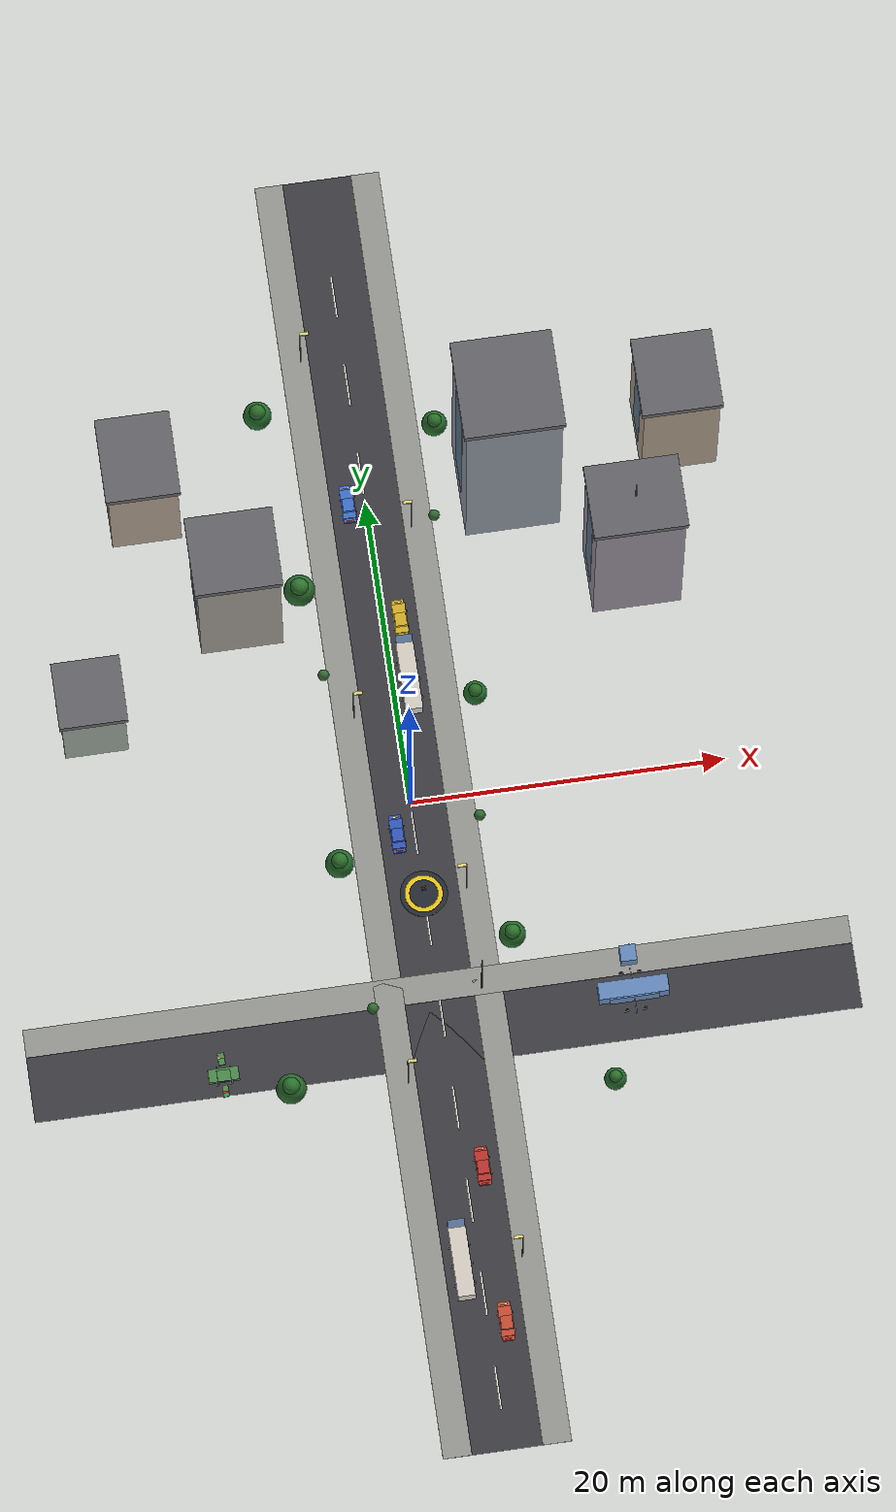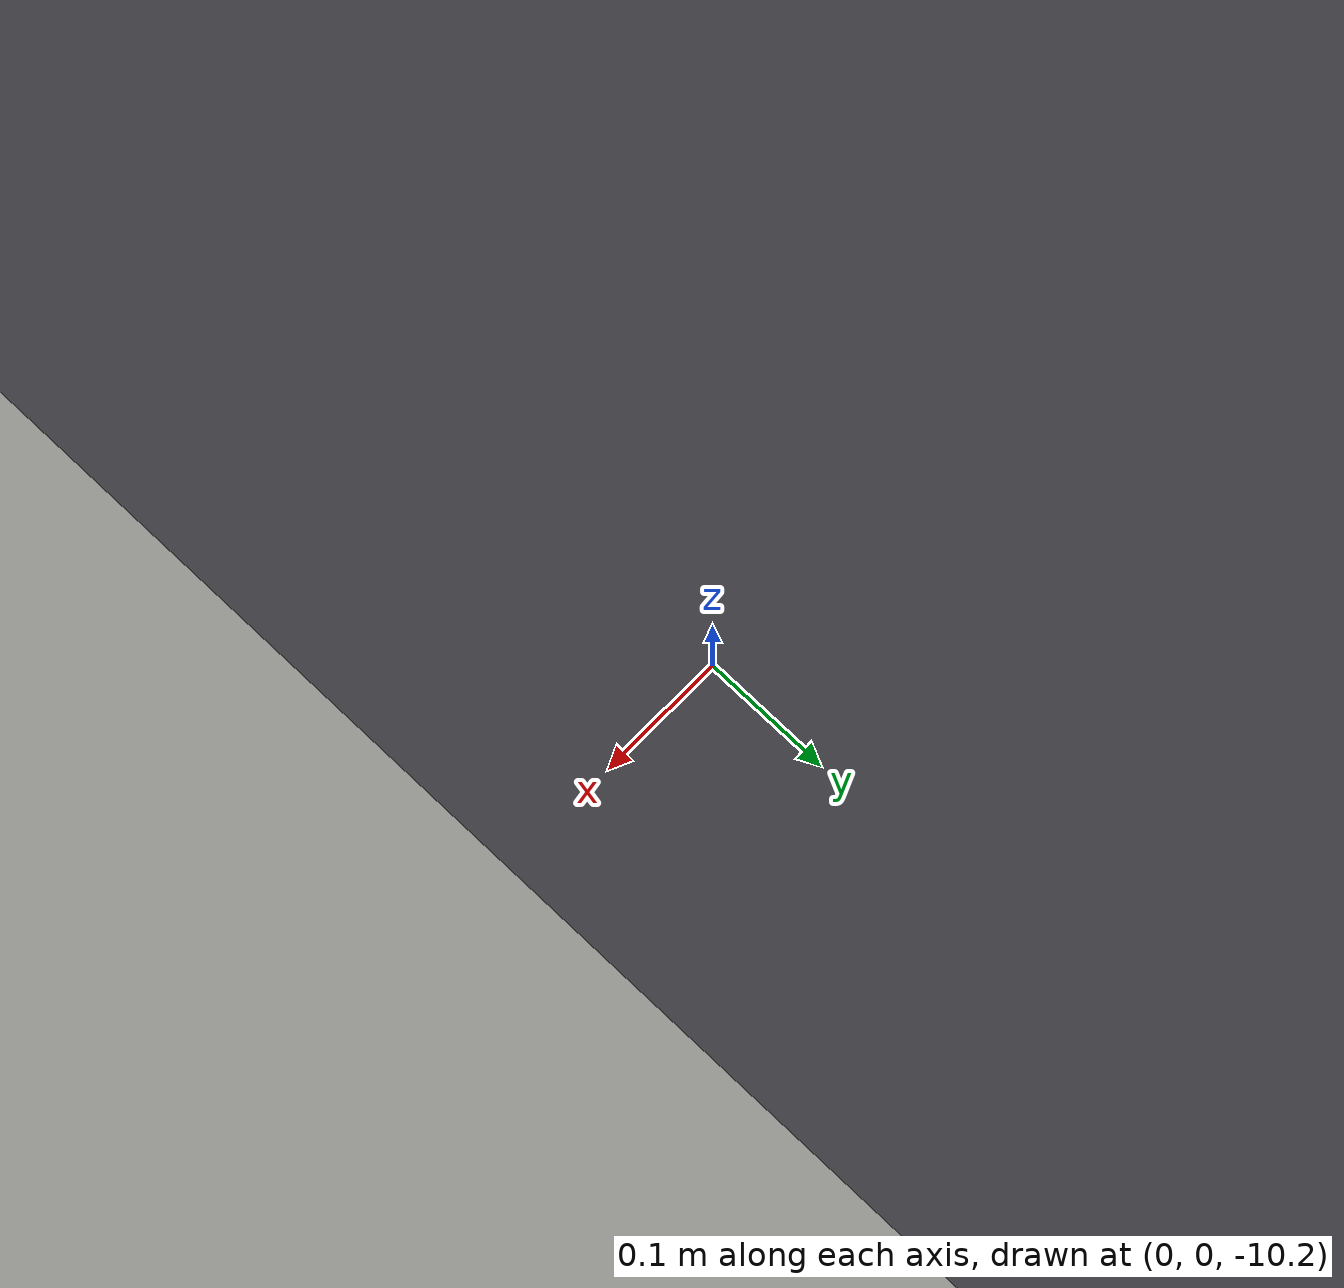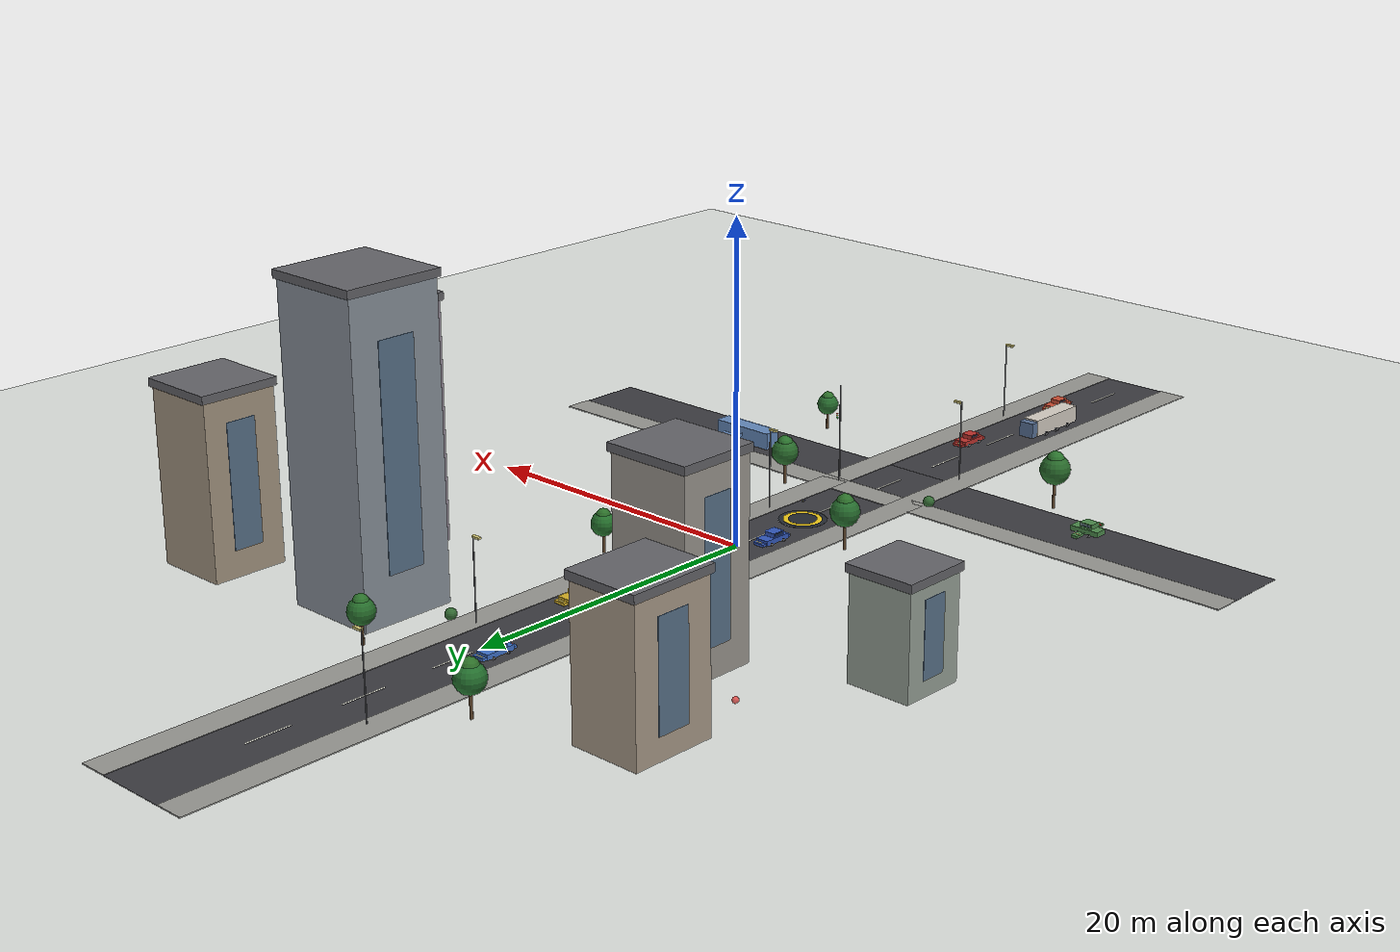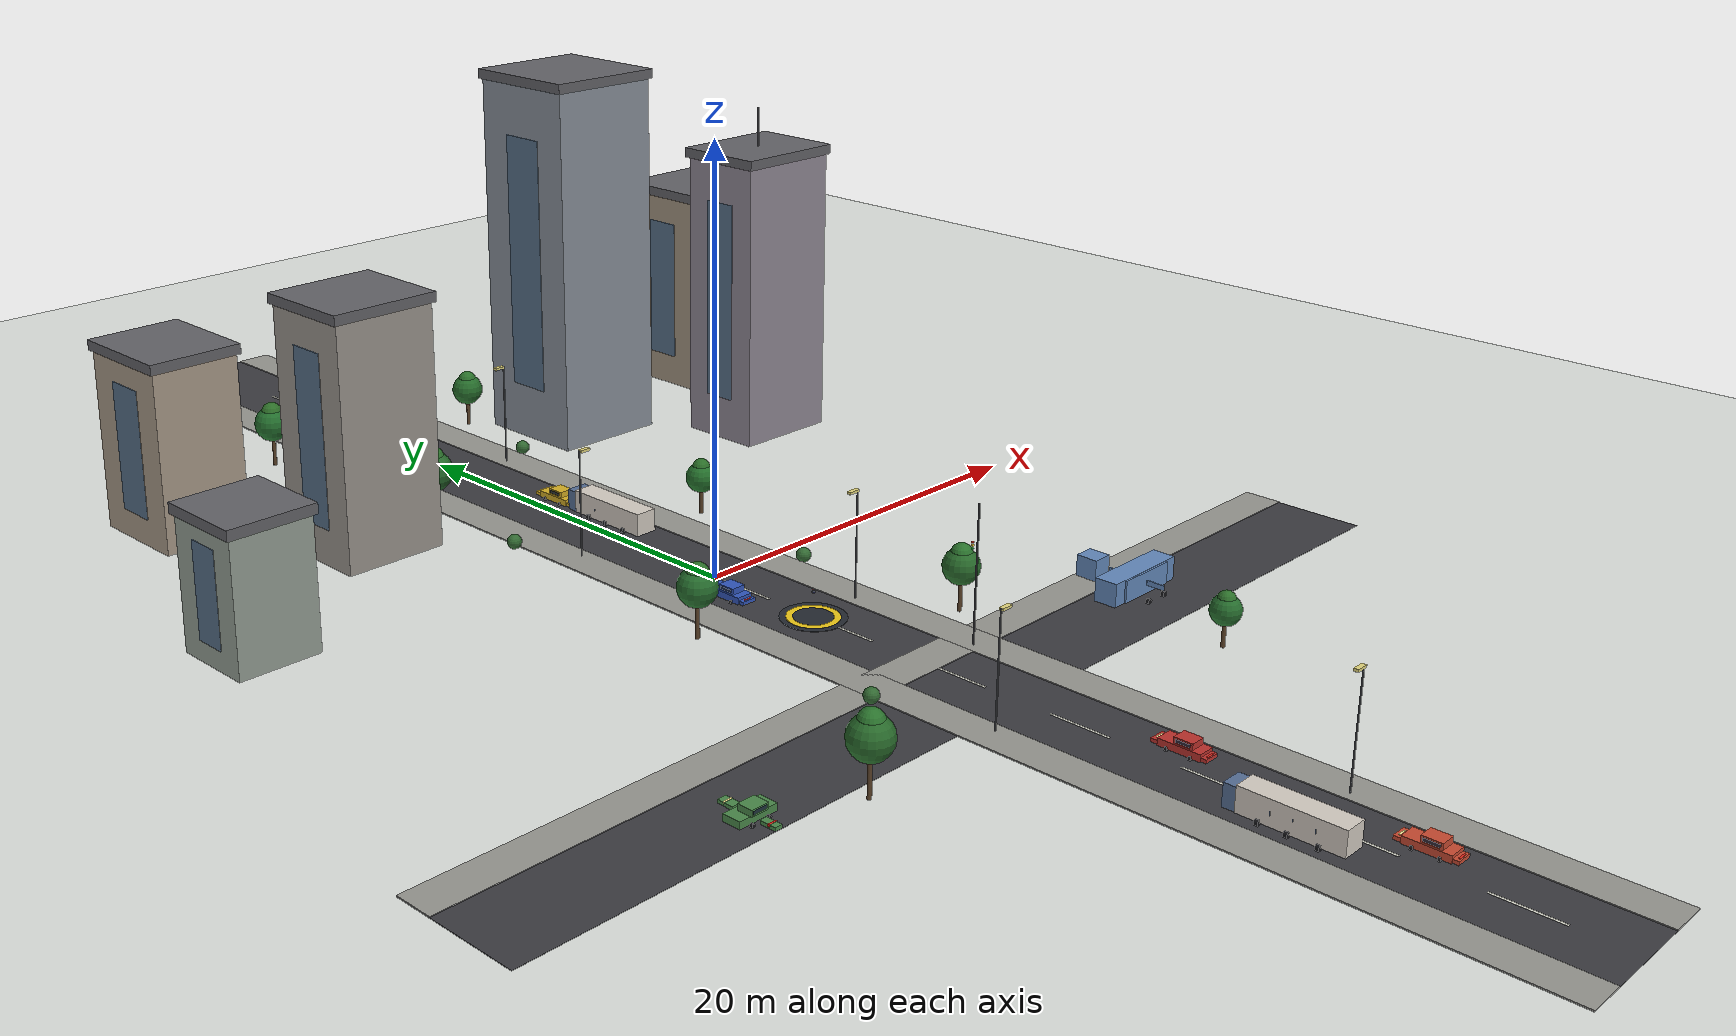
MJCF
<mujoco model="paper_drone_urban_v1">
  <option timestep="1e-4" gravity="0 0 -9.81" integrator="implicitfast"/>
  <visual>
    <headlight ambient="0.4 0.4 0.4" diffuse="0.6 0.6 0.6" specular="0.12 0.12 0.12"/>
    <global offwidth="1920" offheight="1080"/>
    <map znear="0.01" zfar="120"/>
  </visual>
  <asset>
    <texture type="skybox" builtin="gradient" rgb1="0.5 0.6 0.78" rgb2="0.92 0.93 0.96" width="256" height="256"/>
    <texture name="groundtex" type="2d" builtin="checker" rgb1="0.30 0.40 0.26" rgb2="0.36 0.46 0.30" width="200" height="200"/>
    <material name="groundmat" texture="groundtex" texrepeat="14 14" specular="0.05"/>
  </asset>
  <worldbody>
    <light directional="true" castshadow="true" pos="6 6 14" dir="0 0 -1"/>
    <light directional="true" pos="-8 -6 10" dir="0.3 0.2 -1" diffuse="0.25 0.27 0.3"/>
    <geom name="floor" type="plane" size="60 60 0.1" material="groundmat" rgba="0.7 0.75 0.7 1" friction="1.0 0.5 0.5"/>
    <geom name="road_ns" type="box" size="2.2 42 0.01" pos="0 0 0.011" rgba="0.24 0.24 0.26 1" contype="0" conaffinity="0"/>
    <geom name="road_ew" type="box" size="26 2.2 0.01" pos="0 -15 0.011" rgba="0.24 0.24 0.26 1" contype="0" conaffinity="0"/>
    <geom name="dash0" type="box" size="0.06 1.4 0.005" pos="0 -38 0.021" rgba="0.9 0.9 0.85 1" contype="0" conaffinity="0"/>
    <geom name="dash1" type="box" size="0.06 1.4 0.005" pos="0 -32 0.021" rgba="0.9 0.9 0.85 1" contype="0" conaffinity="0"/>
    <geom name="dash2" type="box" size="0.06 1.4 0.005" pos="0 -26 0.021" rgba="0.9 0.9 0.85 1" contype="0" conaffinity="0"/>
    <geom name="dash3" type="box" size="0.06 1.4 0.005" pos="0 -20 0.021" rgba="0.9 0.9 0.85 1" contype="0" conaffinity="0"/>
    <geom name="dash4" type="box" size="0.06 1.4 0.005" pos="0 -14 0.021" rgba="0.9 0.9 0.85 1" contype="0" conaffinity="0"/>
    <geom name="dash5" type="box" size="0.06 1.4 0.005" pos="0 -8 0.021" rgba="0.9 0.9 0.85 1" contype="0" conaffinity="0"/>
    <geom name="dash6" type="box" size="0.06 1.4 0.005" pos="0 -2 0.021" rgba="0.9 0.9 0.85 1" contype="0" conaffinity="0"/>
    <geom name="dash7" type="box" size="0.06 1.4 0.005" pos="0 4 0.021" rgba="0.9 0.9 0.85 1" contype="0" conaffinity="0"/>
    <geom name="dash8" type="box" size="0.06 1.4 0.005" pos="0 10 0.021" rgba="0.9 0.9 0.85 1" contype="0" conaffinity="0"/>
    <geom name="dash9" type="box" size="0.06 1.4 0.005" pos="0 16 0.021" rgba="0.9 0.9 0.85 1" contype="0" conaffinity="0"/>
    <geom name="dash10" type="box" size="0.06 1.4 0.005" pos="0 22 0.021" rgba="0.9 0.9 0.85 1" contype="0" conaffinity="0"/>
    <geom name="dash11" type="box" size="0.06 1.4 0.005" pos="0 28 0.021" rgba="0.9 0.9 0.85 1" contype="0" conaffinity="0"/>
    <geom name="dash12" type="box" size="0.06 1.4 0.005" pos="0 34 0.021" rgba="0.9 0.9 0.85 1" contype="0" conaffinity="0"/>
    <geom name="sidewalk_e" type="box" size="0.9 42 0.03" pos="3.1 0 0.03" rgba="0.6 0.6 0.58 1" friction="1 0.5 0.5"/>
    <geom name="sidewalk_w" type="box" size="0.9 42 0.03" pos="-3.1 0 0.03" rgba="0.6 0.6 0.58 1" friction="1 0.5 0.5"/>
    <geom name="sidewalk_n" type="box" size="26 0.9 0.03" pos="0 -12.1 0.03" rgba="0.6 0.6 0.58 1" friction="1 0.5 0.5"/>
    <geom name="crosswalk" type="box" size="1.8 0.25 0.006" pos="0 -12.6 0.022" rgba="0.9 0.9 0.85 1" contype="0" conaffinity="0"/>
    <geom name="pad_base" type="cylinder" size="1.5 0.02" pos="0 -6 0.02" rgba="0.15 0.17 0.2 1" friction="1 0.5 0.5"/>
    <geom name="pad_ring" type="cylinder" size="1.2 0.025" pos="0 -6 0.026" rgba="0.95 0.8 0.1 1" contype="0" conaffinity="0"/>
    <geom name="pad_inner" type="cylinder" size="0.9 0.028" pos="0 -6 0.028" rgba="0.15 0.17 0.2 1" contype="0" conaffinity="0"/>
    <geom name="bldg_1" type="box" size="2.6 2.4 6.0" pos="-9 14 6.0" rgba="0.62 0.60 0.57 1" friction="1 0.5 0.5"/>
    <geom name="bldg_1_roof" type="box" size="2.75 2.55 0.25" pos="-9 14 12.05" rgba="0.4 0.4 0.42 1" contype="0" conaffinity="0"/>
    <geom name="bldg_1_win" type="box" size="2.6260000000000003 0.96 4.199999999999999" pos="-9 14 6.0" rgba="0.35 0.45 0.55 0.9" contype="0" conaffinity="0"/>
    <geom name="bldg_2" type="box" size="3.0 3.0 9.5" pos="9 20 9.5" rgba="0.55 0.58 0.62 1" friction="1 0.5 0.5"/>
    <geom name="bldg_2_roof" type="box" size="3.15 3.15 0.25" pos="9 20 19.05" rgba="0.4 0.4 0.42 1" contype="0" conaffinity="0"/>
    <geom name="bldg_2_win" type="box" size="3.0300000000000002 1.2000000000000002 6.6499999999999995" pos="9 20 9.5" rgba="0.35 0.45 0.55 0.9" contype="0" conaffinity="0"/>
    <geom name="bldg_3" type="box" size="2.2 2.6 4.5" pos="-14 22 4.5" rgba="0.68 0.62 0.55 1" friction="1 0.5 0.5"/>
    <geom name="bldg_3_roof" type="box" size="2.35 2.75 0.25" pos="-14 22 9.05" rgba="0.4 0.4 0.42 1" contype="0" conaffinity="0"/>
    <geom name="bldg_3_win" type="box" size="2.2220000000000004 1.04 3.15" pos="-14 22 4.5" rgba="0.35 0.45 0.55 0.9" contype="0" conaffinity="0"/>
    <geom name="bldg_4" type="box" size="2.8 2.2 7.5" pos="16 13 7.5" rgba="0.58 0.55 0.6 1" friction="1 0.5 0.5"/>
    <geom name="bldg_4_roof" type="box" size="2.9499999999999997 2.35 0.25" pos="16 13 15.05" rgba="0.4 0.4 0.42 1" contype="0" conaffinity="0"/>
    <geom name="bldg_4_win" type="box" size="2.828 0.8800000000000001 5.25" pos="16 13 7.5" rgba="0.35 0.45 0.55 0.9" contype="0" conaffinity="0"/>
    <geom name="bldg_5" type="box" size="2.4 2.4 5.5" pos="20 22 5.5" rgba="0.66 0.6 0.52 1" friction="1 0.5 0.5"/>
    <geom name="bldg_5_roof" type="box" size="2.55 2.55 0.25" pos="20 22 11.05" rgba="0.4 0.4 0.42 1" contype="0" conaffinity="0"/>
    <geom name="bldg_5_win" type="box" size="2.424 0.96 3.8499999999999996" pos="20 22 5.5" rgba="0.35 0.45 0.55 0.9" contype="0" conaffinity="0"/>
    <geom name="bldg_6" type="box" size="2.0 2.0 3.2" pos="-19 8 3.2" rgba="0.6 0.64 0.6 1" friction="1 0.5 0.5"/>
    <geom name="bldg_6_roof" type="box" size="2.15 2.15 0.25" pos="-19 8 6.45" rgba="0.4 0.4 0.42 1" contype="0" conaffinity="0"/>
    <geom name="bldg_6_win" type="box" size="2.02 0.8 2.2399999999999998" pos="-19 8 3.2" rgba="0.35 0.45 0.55 0.9" contype="0" conaffinity="0"/>
    <geom name="bldg_4_ant" type="cylinder" size="0.05 1.4" pos="16 13 15.9" rgba="0.38 0.38 0.4 1" contype="0" conaffinity="0"/>
    <geom name="tree_0_trunk" type="cylinder" size="0.09 1.4" pos="5 -10 1.4" rgba="0.36 0.26 0.16 1" friction="1 0.5 0.5"/>
    <geom name="tree_0_top" type="sphere" size="0.85" pos="5 -10 2.1224999999999996" rgba="0.16 0.42 0.17 1" friction="1 0.5 0.5"/>
    <geom name="tree_0_top2" type="sphere" size="0.51" pos="5 -10 2.675" rgba="0.17 0.46 0.18 1" contype="0" conaffinity="0"/>
    <geom name="tree_1_trunk" type="cylinder" size="0.09 1.6" pos="-5 -4 1.6" rgba="0.36 0.26 0.16 1" friction="1 0.5 0.5"/>
    <geom name="tree_1_top" type="sphere" size="0.9" pos="-5 -4 2.365" rgba="0.15 0.43 0.18 1" friction="1 0.5 0.5"/>
    <geom name="tree_1_top2" type="sphere" size="0.54" pos="-5 -4 2.95" rgba="0.18 0.45 0.17 1" contype="0" conaffinity="0"/>
    <geom name="tree_2_trunk" type="cylinder" size="0.09 1.2" pos="5 6 1.2" rgba="0.36 0.26 0.16 1" friction="1 0.5 0.5"/>
    <geom name="tree_2_top" type="sphere" size="0.75" pos="5 6 1.8375" rgba="0.14 0.44 0.17 1" friction="1 0.5 0.5"/>
    <geom name="tree_2_top2" type="sphere" size="0.44999999999999996" pos="5 6 2.325" rgba="0.17 0.44 0.16 1" contype="0" conaffinity="0"/>
    <geom name="tree_3_trunk" type="cylinder" size="0.09 1.8" pos="-5 14 1.8" rgba="0.36 0.26 0.16 1" friction="1 0.5 0.5"/>
    <geom name="tree_3_top" type="sphere" size="1.0" pos="-5 14 2.65" rgba="0.16 0.42 0.18 1" friction="1 0.5 0.5"/>
    <geom name="tree_3_top2" type="sphere" size="0.6" pos="-5 14 3.3" rgba="0.18 0.46 0.18 1" contype="0" conaffinity="0"/>
    <geom name="tree_4_trunk" type="cylinder" size="0.09 1.3" pos="5 24 1.3" rgba="0.36 0.26 0.16 1" friction="1 0.5 0.5"/>
    <geom name="tree_4_top" type="sphere" size="0.8" pos="5 24 1.98" rgba="0.15 0.43 0.17 1" friction="1 0.5 0.5"/>
    <geom name="tree_4_top2" type="sphere" size="0.48" pos="5 24 2.5" rgba="0.17 0.45 0.17 1" contype="0" conaffinity="0"/>
    <geom name="tree_5_trunk" type="cylinder" size="0.09 1.5" pos="-6 26 1.5" rgba="0.36 0.26 0.16 1" friction="1 0.5 0.5"/>
    <geom name="tree_5_top" type="sphere" size="0.9" pos="-6 26 2.265" rgba="0.14 0.44 0.18 1" friction="1 0.5 0.5"/>
    <geom name="tree_5_top2" type="sphere" size="0.54" pos="-6 26 2.85" rgba="0.18 0.44 0.16 1" contype="0" conaffinity="0"/>
    <geom name="tree_6_trunk" type="cylinder" size="0.09 1.7" pos="-10 -18 1.7" rgba="0.36 0.26 0.16 1" friction="1 0.5 0.5"/>
    <geom name="tree_6_top" type="sphere" size="0.95" pos="-10 -18 2.5075" rgba="0.16 0.42 0.17 1" friction="1 0.5 0.5"/>
    <geom name="tree_6_top2" type="sphere" size="0.57" pos="-10 -18 3.125" rgba="0.17 0.46 0.18 1" contype="0" conaffinity="0"/>
    <geom name="tree_7_trunk" type="cylinder" size="0.09 1.1" pos="10 -20 1.1" rgba="0.36 0.26 0.16 1" friction="1 0.5 0.5"/>
    <geom name="tree_7_top" type="sphere" size="0.7" pos="10 -20 1.695" rgba="0.15 0.43 0.18 1" friction="1 0.5 0.5"/>
    <geom name="tree_7_top2" type="sphere" size="0.42" pos="10 -20 2.15" rgba="0.18 0.45 0.17 1" contype="0" conaffinity="0"/>
    <geom name="bush_0" type="sphere" size="0.35" pos="4.2 -1.5 0.3" rgba="0.2 0.42 0.2 1" contype="0" conaffinity="0"/>
    <geom name="bush_1" type="sphere" size="0.35" pos="-4.2 9 0.3" rgba="0.2 0.42 0.2 1" contype="0" conaffinity="0"/>
    <geom name="bush_2" type="sphere" size="0.35" pos="4.2 18.5 0.3" rgba="0.2 0.42 0.2 1" contype="0" conaffinity="0"/>
    <geom name="bush_3" type="sphere" size="0.35" pos="-4.2 -13 0.3" rgba="0.2 0.42 0.2 1" contype="0" conaffinity="0"/>
    <geom name="lamp_0_pole" type="cylinder" size="0.035 2.6" pos="2.7 -30 2.6" rgba="0.35 0.36 0.38 1" friction="1 0.5 0.5"/>
    <geom name="lamp_0_head" type="box" size="0.28 0.1 0.06" pos="2.42 -30 5.15" rgba="0.9 0.85 0.5 1" contype="0" conaffinity="0"/>
    <geom name="lamp_1_pole" type="cylinder" size="0.035 2.6" pos="-2.7 -18 2.6" rgba="0.35 0.36 0.38 1" friction="1 0.5 0.5"/>
    <geom name="lamp_1_head" type="box" size="0.28 0.1 0.06" pos="-2.42 -18 5.15" rgba="0.9 0.85 0.5 1" contype="0" conaffinity="0"/>
    <geom name="lamp_2_pole" type="cylinder" size="0.035 2.6" pos="2.7 -6 2.6" rgba="0.35 0.36 0.38 1" friction="1 0.5 0.5"/>
    <geom name="lamp_2_head" type="box" size="0.28 0.1 0.06" pos="2.42 -6 5.15" rgba="0.9 0.85 0.5 1" contype="0" conaffinity="0"/>
    <geom name="lamp_3_pole" type="cylinder" size="0.035 2.6" pos="-2.7 6 2.6" rgba="0.35 0.36 0.38 1" friction="1 0.5 0.5"/>
    <geom name="lamp_3_head" type="box" size="0.28 0.1 0.06" pos="-2.42 6 5.15" rgba="0.9 0.85 0.5 1" contype="0" conaffinity="0"/>
    <geom name="lamp_4_pole" type="cylinder" size="0.035 2.6" pos="2.7 18 2.6" rgba="0.35 0.36 0.38 1" friction="1 0.5 0.5"/>
    <geom name="lamp_4_head" type="box" size="0.28 0.1 0.06" pos="2.42 18 5.15" rgba="0.9 0.85 0.5 1" contype="0" conaffinity="0"/>
    <geom name="lamp_5_pole" type="cylinder" size="0.035 2.6" pos="-2.7 30 2.6" rgba="0.35 0.36 0.38 1" friction="1 0.5 0.5"/>
    <geom name="lamp_5_head" type="box" size="0.28 0.1 0.06" pos="-2.42 30 5.15" rgba="0.9 0.85 0.5 1" contype="0" conaffinity="0"/>
    <geom name="tlight_pole" type="cylinder" size="0.04 3.2" pos="2.7 -12.6 3.2" rgba="0.3 0.3 0.32 1" friction="1 0.5 0.5"/>
    <geom name="tlight_0" type="sphere" size="0.055" pos="2.7 -12.35 4.6" rgba="0.9 0.2 0.15 1" contype="0" conaffinity="0"/>
    <geom name="tlight_1" type="sphere" size="0.055" pos="2.7 -12.35 4.46" rgba="0.95 0.8 0.2 1" contype="0" conaffinity="0"/>
    <geom name="tlight_2" type="sphere" size="0.055" pos="2.7 -12.35 4.319999999999999" rgba="0.2 0.8 0.3 1" contype="0" conaffinity="0"/>
  <body name="car_1" pos="1.1 -24 0">
    <freejoint name="car_1_j"/>
    <geom name="car_1" type="box" size="0.42 0.95 0.16" pos="0 0 0.25" rgba="0.75 0.2 0.18 1" euler="0 0 0" friction="1 0.5 0.5"/>
    <geom name="car_1_hood" type="box" size="0.378 0.209 0.08" pos="0 1.05 0.194" rgba="0.75 0.2 0.18 1" euler="0 0 0" contype="0" conaffinity="0" friction="1 0.5 0.5"/>
    <geom name="car_1_trunk" type="box" size="0.378 0.17099999999999999 0.08" pos="0 -1.03 0.194" rgba="0.75 0.2 0.18 1" euler="0 0 0" contype="0" conaffinity="0" friction="1 0.5 0.5"/>
    <geom name="car_1_cabin" type="box" size="0.36 0.42 0.14" pos="0 -0.1425 0.55" rgba="0.75 0.2 0.18 1" euler="0 0 0" contype="0" conaffinity="0" friction="1 0.5 0.5"/>
    <geom name="car_1_glass" type="box" size="0.36719999999999997 0.336 0.07700000000000001" pos="0 -0.1425 0.543" rgba="0.15 0.2 0.28 0.85" euler="0 0 0" contype="0" conaffinity="0" friction="1 0.5 0.5"/>
    <geom name="car_1_w0" type="cylinder" size="0.09 0.06" pos="0.42 0.5225 0.09" rgba="0.08 0.08 0.09 1" euler="90 0 0" contype="0" conaffinity="0" friction="1 0.5 0.5"/>
    <geom name="car_1_w1" type="cylinder" size="0.09 0.06" pos="0.42 -0.5225 0.09" rgba="0.08 0.08 0.09 1" euler="90 0 0" contype="0" conaffinity="0" friction="1 0.5 0.5"/>
    <geom name="car_1_w2" type="cylinder" size="0.09 0.06" pos="-0.42 0.5225 0.09" rgba="0.08 0.08 0.09 1" euler="90 0 0" contype="0" conaffinity="0" friction="1 0.5 0.5"/>
    <geom name="car_1_w3" type="cylinder" size="0.09 0.06" pos="-0.42 -0.5225 0.09" rgba="0.08 0.08 0.09 1" euler="90 0 0" contype="0" conaffinity="0" friction="1 0.5 0.5"/>
    <geom name="car_1_hl" type="box" size="0.21 0.04 0.04" pos="0 1.1099999999999999 0.25" rgba="1 0.95 0.6 1" contype="0" conaffinity="0" friction="1 0.5 0.5"/>
    <geom name="car_1_tl" type="box" size="0.21 0.04 0.04" pos="0 -1.1099999999999999 0.25" rgba="0.9 0.15 0.1 1" contype="0" conaffinity="0" friction="1 0.5 0.5"/>
  </body>
  <body name="car_2" pos="-1.1 -2 0">
    <freejoint name="car_2_j"/>
    <geom name="car_2" type="box" size="0.42 0.95 0.16" pos="0 0 0.25" rgba="0.2 0.35 0.75 1" euler="0 0 180" friction="1 0.5 0.5"/>
    <geom name="car_2_hood" type="box" size="0.378 0.209 0.08" pos="0 1.05 0.194" rgba="0.2 0.35 0.75 1" euler="0 0 180" contype="0" conaffinity="0" friction="1 0.5 0.5"/>
    <geom name="car_2_trunk" type="box" size="0.378 0.17099999999999999 0.08" pos="0 -1.03 0.194" rgba="0.2 0.35 0.75 1" euler="0 0 180" contype="0" conaffinity="0" friction="1 0.5 0.5"/>
    <geom name="car_2_cabin" type="box" size="0.36 0.42 0.14" pos="0 -0.1425 0.55" rgba="0.2 0.35 0.75 1" euler="0 0 180" contype="0" conaffinity="0" friction="1 0.5 0.5"/>
    <geom name="car_2_glass" type="box" size="0.36719999999999997 0.336 0.07700000000000001" pos="0 -0.1425 0.543" rgba="0.15 0.2 0.28 0.85" euler="0 0 180" contype="0" conaffinity="0" friction="1 0.5 0.5"/>
    <geom name="car_2_w0" type="cylinder" size="0.09 0.06" pos="0.42 0.5225 0.09" rgba="0.08 0.08 0.09 1" euler="90 0 0" contype="0" conaffinity="0" friction="1 0.5 0.5"/>
    <geom name="car_2_w1" type="cylinder" size="0.09 0.06" pos="0.42 -0.5225 0.09" rgba="0.08 0.08 0.09 1" euler="90 0 0" contype="0" conaffinity="0" friction="1 0.5 0.5"/>
    <geom name="car_2_w2" type="cylinder" size="0.09 0.06" pos="-0.42 0.5225 0.09" rgba="0.08 0.08 0.09 1" euler="90 0 0" contype="0" conaffinity="0" friction="1 0.5 0.5"/>
    <geom name="car_2_w3" type="cylinder" size="0.09 0.06" pos="-0.42 -0.5225 0.09" rgba="0.08 0.08 0.09 1" euler="90 0 0" contype="0" conaffinity="0" friction="1 0.5 0.5"/>
    <geom name="car_2_hl" type="box" size="0.21 0.04 0.04" pos="0 1.1099999999999999 0.25" rgba="1 0.95 0.6 1" contype="0" conaffinity="0" friction="1 0.5 0.5"/>
    <geom name="car_2_tl" type="box" size="0.21 0.04 0.04" pos="0 -1.1099999999999999 0.25" rgba="0.9 0.15 0.1 1" contype="0" conaffinity="0" friction="1 0.5 0.5"/>
  </body>
  <body name="car_3" pos="1.1 12 0">
    <freejoint name="car_3_j"/>
    <geom name="car_3" type="box" size="0.42 0.95 0.16" pos="0 0 0.25" rgba="0.85 0.7 0.15 1" euler="0 0 0" friction="1 0.5 0.5"/>
    <geom name="car_3_hood" type="box" size="0.378 0.209 0.08" pos="0 1.05 0.194" rgba="0.85 0.7 0.15 1" euler="0 0 0" contype="0" conaffinity="0" friction="1 0.5 0.5"/>
    <geom name="car_3_trunk" type="box" size="0.378 0.17099999999999999 0.08" pos="0 -1.03 0.194" rgba="0.85 0.7 0.15 1" euler="0 0 0" contype="0" conaffinity="0" friction="1 0.5 0.5"/>
    <geom name="car_3_cabin" type="box" size="0.36 0.42 0.14" pos="0 -0.1425 0.55" rgba="0.85 0.7 0.15 1" euler="0 0 0" contype="0" conaffinity="0" friction="1 0.5 0.5"/>
    <geom name="car_3_glass" type="box" size="0.36719999999999997 0.336 0.07700000000000001" pos="0 -0.1425 0.543" rgba="0.15 0.2 0.28 0.85" euler="0 0 0" contype="0" conaffinity="0" friction="1 0.5 0.5"/>
    <geom name="car_3_w0" type="cylinder" size="0.09 0.06" pos="0.42 0.5225 0.09" rgba="0.08 0.08 0.09 1" euler="90 0 0" contype="0" conaffinity="0" friction="1 0.5 0.5"/>
    <geom name="car_3_w1" type="cylinder" size="0.09 0.06" pos="0.42 -0.5225 0.09" rgba="0.08 0.08 0.09 1" euler="90 0 0" contype="0" conaffinity="0" friction="1 0.5 0.5"/>
    <geom name="car_3_w2" type="cylinder" size="0.09 0.06" pos="-0.42 0.5225 0.09" rgba="0.08 0.08 0.09 1" euler="90 0 0" contype="0" conaffinity="0" friction="1 0.5 0.5"/>
    <geom name="car_3_w3" type="cylinder" size="0.09 0.06" pos="-0.42 -0.5225 0.09" rgba="0.08 0.08 0.09 1" euler="90 0 0" contype="0" conaffinity="0" friction="1 0.5 0.5"/>
    <geom name="car_3_hl" type="box" size="0.21 0.04 0.04" pos="0 1.1099999999999999 0.25" rgba="1 0.95 0.6 1" contype="0" conaffinity="0" friction="1 0.5 0.5"/>
    <geom name="car_3_tl" type="box" size="0.21 0.04 0.04" pos="0 -1.1099999999999999 0.25" rgba="0.9 0.15 0.1 1" contype="0" conaffinity="0" friction="1 0.5 0.5"/>
  </body>
  <body name="car_4" pos="-14 -15.9 0">
    <freejoint name="car_4_j"/>
    <geom name="car_4" type="box" size="0.42 0.95 0.16" pos="0 0 0.25" rgba="0.3 0.55 0.3 1" euler="0 0 90" friction="1 0.5 0.5"/>
    <geom name="car_4_hood" type="box" size="0.378 0.209 0.08" pos="0 1.05 0.194" rgba="0.3 0.55 0.3 1" euler="0 0 90" contype="0" conaffinity="0" friction="1 0.5 0.5"/>
    <geom name="car_4_trunk" type="box" size="0.378 0.17099999999999999 0.08" pos="0 -1.03 0.194" rgba="0.3 0.55 0.3 1" euler="0 0 90" contype="0" conaffinity="0" friction="1 0.5 0.5"/>
    <geom name="car_4_cabin" type="box" size="0.36 0.42 0.14" pos="0 -0.1425 0.55" rgba="0.3 0.55 0.3 1" euler="0 0 90" contype="0" conaffinity="0" friction="1 0.5 0.5"/>
    <geom name="car_4_glass" type="box" size="0.36719999999999997 0.336 0.07700000000000001" pos="0 -0.1425 0.543" rgba="0.15 0.2 0.28 0.85" euler="0 0 90" contype="0" conaffinity="0" friction="1 0.5 0.5"/>
    <geom name="car_4_w0" type="cylinder" size="0.09 0.06" pos="0.42 0.5225 0.09" rgba="0.08 0.08 0.09 1" euler="90 0 0" contype="0" conaffinity="0" friction="1 0.5 0.5"/>
    <geom name="car_4_w1" type="cylinder" size="0.09 0.06" pos="0.42 -0.5225 0.09" rgba="0.08 0.08 0.09 1" euler="90 0 0" contype="0" conaffinity="0" friction="1 0.5 0.5"/>
    <geom name="car_4_w2" type="cylinder" size="0.09 0.06" pos="-0.42 0.5225 0.09" rgba="0.08 0.08 0.09 1" euler="90 0 0" contype="0" conaffinity="0" friction="1 0.5 0.5"/>
    <geom name="car_4_w3" type="cylinder" size="0.09 0.06" pos="-0.42 -0.5225 0.09" rgba="0.08 0.08 0.09 1" euler="90 0 0" contype="0" conaffinity="0" friction="1 0.5 0.5"/>
    <geom name="car_4_hl" type="box" size="0.21 0.04 0.04" pos="0 1.1099999999999999 0.25" rgba="1 0.95 0.6 1" contype="0" conaffinity="0" friction="1 0.5 0.5"/>
    <geom name="car_4_tl" type="box" size="0.21 0.04 0.04" pos="0 -1.1099999999999999 0.25" rgba="0.9 0.15 0.1 1" contype="0" conaffinity="0" friction="1 0.5 0.5"/>
  </body>
  <body name="truck_1" pos="-1.1 -30 0">
    <freejoint name="truck_1_j"/>
    <geom name="truck_1" type="box" size="0.55 2.1999999999999997 0.55" pos="0 -0.075 0.68" rgba="0.85 0.82 0.78 1" euler="0 0 0" friction="1 0.5 0.5"/>
    <geom name="truck_1_cab" type="box" size="0.52 0.5 0.5" pos="0 2.17 0.63" rgba="0.35 0.45 0.6 1" euler="0 0 0" contype="0" conaffinity="0" friction="1 0.5 0.5"/>
    <geom name="truck_1_cabglass" type="box" size="0.468 0.15 0.275" pos="0 2.275 0.755" rgba="0.15 0.2 0.28 0.85" euler="0 0 0" contype="0" conaffinity="0" friction="1 0.5 0.5"/>
    <geom name="truck_1_box" type="box" size="0.539 1.55 0.528" pos="0 -0.175 0.68" rgba="0.85 0.82 0.78 1" euler="0 0 0" contype="0" conaffinity="0" friction="1 0.5 0.5"/>
    <geom name="truck_1_rib0" type="box" size="0.55 0.015 0.12" pos="0 -1.075 0.68" rgba="0.35 0.45 0.6 1" euler="0 0 0" contype="0" conaffinity="0" friction="1 0.5 0.5"/>
    <geom name="truck_1_rib1" type="box" size="0.55 0.015 0.12" pos="0 -0.175 0.68" rgba="0.35 0.45 0.6 1" euler="0 0 0" contype="0" conaffinity="0" friction="1 0.5 0.5"/>
    <geom name="truck_1_rib2" type="box" size="0.55 0.015 0.12" pos="0 0.7250000000000001 0.68" rgba="0.35 0.45 0.6 1" euler="0 0 0" contype="0" conaffinity="0" friction="1 0.5 0.5"/>
    <geom name="truck_1_w0r" type="cylinder" size="0.13 0.08" pos="0.5700000000000001 1.1625 0.13" rgba="0.08 0.08 0.09 1" euler="90 0 0" contype="0" conaffinity="0" friction="1 0.5 0.5"/>
    <geom name="truck_1_w0l" type="cylinder" size="0.13 0.08" pos="-0.5700000000000001 1.1625 0.13" rgba="0.08 0.08 0.09 1" euler="90 0 0" contype="0" conaffinity="0" friction="1 0.5 0.5"/>
    <geom name="truck_1_w1r" type="cylinder" size="0.13 0.08" pos="0.5700000000000001 0.0 0.13" rgba="0.08 0.08 0.09 1" euler="90 0 0" contype="0" conaffinity="0" friction="1 0.5 0.5"/>
    <geom name="truck_1_w1l" type="cylinder" size="0.13 0.08" pos="-0.5700000000000001 0.0 0.13" rgba="0.08 0.08 0.09 1" euler="90 0 0" contype="0" conaffinity="0" friction="1 0.5 0.5"/>
    <geom name="truck_1_w2r" type="cylinder" size="0.13 0.08" pos="0.5700000000000001 -1.2400000000000002 0.13" rgba="0.08 0.08 0.09 1" euler="90 0 0" contype="0" conaffinity="0" friction="1 0.5 0.5"/>
    <geom name="truck_1_w2l" type="cylinder" size="0.13 0.08" pos="-0.5700000000000001 -1.2400000000000002 0.13" rgba="0.08 0.08 0.09 1" euler="90 0 0" contype="0" conaffinity="0" friction="1 0.5 0.5"/>
    <geom name="truck_1_hl" type="box" size="0.08 0.04 0.05" pos="0 2.5999999999999996 0.48" rgba="1 0.95 0.6 1" contype="0" conaffinity="0" friction="1 0.5 0.5"/>
  </body>
  <body name="truck_2" pos="12 -14.1 0">
    <freejoint name="truck_2_j"/>
    <geom name="truck_2" type="box" size="0.55 2.1999999999999997 0.55" pos="0 -0.075 0.68" rgba="0.4 0.55 0.75 1" euler="0 0 90" friction="1 0.5 0.5"/>
    <geom name="truck_2_cab" type="box" size="0.52 0.5 0.5" pos="0 2.17 0.63" rgba="0.4 0.55 0.75 1" euler="0 0 90" contype="0" conaffinity="0" friction="1 0.5 0.5"/>
    <geom name="truck_2_cabglass" type="box" size="0.468 0.15 0.275" pos="0 2.275 0.755" rgba="0.15 0.2 0.28 0.85" euler="0 0 90" contype="0" conaffinity="0" friction="1 0.5 0.5"/>
    <geom name="truck_2_box" type="box" size="0.539 1.55 0.528" pos="0 -0.175 0.68" rgba="0.4 0.55 0.75 1" euler="0 0 90" contype="0" conaffinity="0" friction="1 0.5 0.5"/>
    <geom name="truck_2_rib0" type="box" size="0.55 0.015 0.12" pos="0 -1.075 0.68" rgba="0.4 0.55 0.75 1" euler="0 0 90" contype="0" conaffinity="0" friction="1 0.5 0.5"/>
    <geom name="truck_2_rib1" type="box" size="0.55 0.015 0.12" pos="0 -0.175 0.68" rgba="0.4 0.55 0.75 1" euler="0 0 90" contype="0" conaffinity="0" friction="1 0.5 0.5"/>
    <geom name="truck_2_rib2" type="box" size="0.55 0.015 0.12" pos="0 0.7250000000000001 0.68" rgba="0.4 0.55 0.75 1" euler="0 0 90" contype="0" conaffinity="0" friction="1 0.5 0.5"/>
    <geom name="truck_2_w0r" type="cylinder" size="0.13 0.08" pos="0.5700000000000001 1.1625 0.13" rgba="0.08 0.08 0.09 1" euler="90 0 0" contype="0" conaffinity="0" friction="1 0.5 0.5"/>
    <geom name="truck_2_w0l" type="cylinder" size="0.13 0.08" pos="-0.5700000000000001 1.1625 0.13" rgba="0.08 0.08 0.09 1" euler="90 0 0" contype="0" conaffinity="0" friction="1 0.5 0.5"/>
    <geom name="truck_2_w1r" type="cylinder" size="0.13 0.08" pos="0.5700000000000001 0.0 0.13" rgba="0.08 0.08 0.09 1" euler="90 0 0" contype="0" conaffinity="0" friction="1 0.5 0.5"/>
    <geom name="truck_2_w1l" type="cylinder" size="0.13 0.08" pos="-0.5700000000000001 0.0 0.13" rgba="0.08 0.08 0.09 1" euler="90 0 0" contype="0" conaffinity="0" friction="1 0.5 0.5"/>
    <geom name="truck_2_w2r" type="cylinder" size="0.13 0.08" pos="0.5700000000000001 -1.2400000000000002 0.13" rgba="0.08 0.08 0.09 1" euler="90 0 0" contype="0" conaffinity="0" friction="1 0.5 0.5"/>
    <geom name="truck_2_w2l" type="cylinder" size="0.13 0.08" pos="-0.5700000000000001 -1.2400000000000002 0.13" rgba="0.08 0.08 0.09 1" euler="90 0 0" contype="0" conaffinity="0" friction="1 0.5 0.5"/>
    <geom name="truck_2_hl" type="box" size="0.08 0.04 0.05" pos="0 2.5999999999999996 0.48" rgba="1 0.95 0.6 1" contype="0" conaffinity="0" friction="1 0.5 0.5"/>
  </body>
  <body name="car_m1" pos="1.1 -34 0">
    <freejoint name="car_m1_j"/>
    <geom name="car_m1" type="box" size="0.42 0.95 0.16" pos="0 0 0.25" rgba="0.8 0.3 0.2 1" euler="0 0 0" friction="1 0.5 0.5"/>
    <geom name="car_m1_hood" type="box" size="0.378 0.209 0.08" pos="0 1.05 0.194" rgba="0.8 0.3 0.2 1" euler="0 0 0" contype="0" conaffinity="0" friction="1 0.5 0.5"/>
    <geom name="car_m1_trunk" type="box" size="0.378 0.17099999999999999 0.08" pos="0 -1.03 0.194" rgba="0.8 0.3 0.2 1" euler="0 0 0" contype="0" conaffinity="0" friction="1 0.5 0.5"/>
    <geom name="car_m1_cabin" type="box" size="0.36 0.42 0.14" pos="0 -0.1425 0.55" rgba="0.8 0.3 0.2 1" euler="0 0 0" contype="0" conaffinity="0" friction="1 0.5 0.5"/>
    <geom name="car_m1_glass" type="box" size="0.36719999999999997 0.336 0.07700000000000001" pos="0 -0.1425 0.543" rgba="0.15 0.2 0.28 0.85" euler="0 0 0" contype="0" conaffinity="0" friction="1 0.5 0.5"/>
    <geom name="car_m1_w0" type="cylinder" size="0.09 0.06" pos="0.42 0.5225 0.09" rgba="0.08 0.08 0.09 1" euler="90 0 0" contype="0" conaffinity="0" friction="1 0.5 0.5"/>
    <geom name="car_m1_w1" type="cylinder" size="0.09 0.06" pos="0.42 -0.5225 0.09" rgba="0.08 0.08 0.09 1" euler="90 0 0" contype="0" conaffinity="0" friction="1 0.5 0.5"/>
    <geom name="car_m1_w2" type="cylinder" size="0.09 0.06" pos="-0.42 0.5225 0.09" rgba="0.08 0.08 0.09 1" euler="90 0 0" contype="0" conaffinity="0" friction="1 0.5 0.5"/>
    <geom name="car_m1_w3" type="cylinder" size="0.09 0.06" pos="-0.42 -0.5225 0.09" rgba="0.08 0.08 0.09 1" euler="90 0 0" contype="0" conaffinity="0" friction="1 0.5 0.5"/>
    <geom name="car_m1_hl" type="box" size="0.21 0.04 0.04" pos="0 1.1099999999999999 0.25" rgba="1 0.95 0.6 1" contype="0" conaffinity="0" friction="1 0.5 0.5"/>
    <geom name="car_m1_tl" type="box" size="0.21 0.04 0.04" pos="0 -1.1099999999999999 0.25" rgba="0.9 0.15 0.1 1" contype="0" conaffinity="0" friction="1 0.5 0.5"/>
  </body>
  <body name="car_m2" pos="-1.1 20 0">
    <freejoint name="car_m2_j"/>
    <geom name="car_m2" type="box" size="0.42 0.95 0.16" pos="0 0 0.25" rgba="0.25 0.45 0.8 1" euler="0 0 180" friction="1 0.5 0.5"/>
    <geom name="car_m2_hood" type="box" size="0.378 0.209 0.08" pos="0 1.05 0.194" rgba="0.25 0.45 0.8 1" euler="0 0 180" contype="0" conaffinity="0" friction="1 0.5 0.5"/>
    <geom name="car_m2_trunk" type="box" size="0.378 0.17099999999999999 0.08" pos="0 -1.03 0.194" rgba="0.25 0.45 0.8 1" euler="0 0 180" contype="0" conaffinity="0" friction="1 0.5 0.5"/>
    <geom name="car_m2_cabin" type="box" size="0.36 0.42 0.14" pos="0 -0.1425 0.55" rgba="0.25 0.45 0.8 1" euler="0 0 180" contype="0" conaffinity="0" friction="1 0.5 0.5"/>
    <geom name="car_m2_glass" type="box" size="0.36719999999999997 0.336 0.07700000000000001" pos="0 -0.1425 0.543" rgba="0.15 0.2 0.28 0.85" euler="0 0 180" contype="0" conaffinity="0" friction="1 0.5 0.5"/>
    <geom name="car_m2_w0" type="cylinder" size="0.09 0.06" pos="0.42 0.5225 0.09" rgba="0.08 0.08 0.09 1" euler="90 0 0" contype="0" conaffinity="0" friction="1 0.5 0.5"/>
    <geom name="car_m2_w1" type="cylinder" size="0.09 0.06" pos="0.42 -0.5225 0.09" rgba="0.08 0.08 0.09 1" euler="90 0 0" contype="0" conaffinity="0" friction="1 0.5 0.5"/>
    <geom name="car_m2_w2" type="cylinder" size="0.09 0.06" pos="-0.42 0.5225 0.09" rgba="0.08 0.08 0.09 1" euler="90 0 0" contype="0" conaffinity="0" friction="1 0.5 0.5"/>
    <geom name="car_m2_w3" type="cylinder" size="0.09 0.06" pos="-0.42 -0.5225 0.09" rgba="0.08 0.08 0.09 1" euler="90 0 0" contype="0" conaffinity="0" friction="1 0.5 0.5"/>
    <geom name="car_m2_hl" type="box" size="0.21 0.04 0.04" pos="0 1.1099999999999999 0.25" rgba="1 0.95 0.6 1" contype="0" conaffinity="0" friction="1 0.5 0.5"/>
    <geom name="car_m2_tl" type="box" size="0.21 0.04 0.04" pos="0 -1.1099999999999999 0.25" rgba="0.9 0.15 0.1 1" contype="0" conaffinity="0" friction="1 0.5 0.5"/>
  </body>
  <body name="truck_m1" pos="1.1 8 0">
    <freejoint name="truck_m1_j"/>
    <geom name="truck_m1" type="box" size="0.55 2.1999999999999997 0.55" pos="0 -0.075 0.68" rgba="0.85 0.82 0.78 1" euler="0 0 0" friction="1 0.5 0.5"/>
    <geom name="truck_m1_cab" type="box" size="0.52 0.5 0.5" pos="0 2.17 0.63" rgba="0.35 0.45 0.6 1" euler="0 0 0" contype="0" conaffinity="0" friction="1 0.5 0.5"/>
    <geom name="truck_m1_cabglass" type="box" size="0.468 0.15 0.275" pos="0 2.275 0.755" rgba="0.15 0.2 0.28 0.85" euler="0 0 0" contype="0" conaffinity="0" friction="1 0.5 0.5"/>
    <geom name="truck_m1_box" type="box" size="0.539 1.55 0.528" pos="0 -0.175 0.68" rgba="0.85 0.82 0.78 1" euler="0 0 0" contype="0" conaffinity="0" friction="1 0.5 0.5"/>
    <geom name="truck_m1_rib0" type="box" size="0.55 0.015 0.12" pos="0 -1.075 0.68" rgba="0.35 0.45 0.6 1" euler="0 0 0" contype="0" conaffinity="0" friction="1 0.5 0.5"/>
    <geom name="truck_m1_rib1" type="box" size="0.55 0.015 0.12" pos="0 -0.175 0.68" rgba="0.35 0.45 0.6 1" euler="0 0 0" contype="0" conaffinity="0" friction="1 0.5 0.5"/>
    <geom name="truck_m1_rib2" type="box" size="0.55 0.015 0.12" pos="0 0.7250000000000001 0.68" rgba="0.35 0.45 0.6 1" euler="0 0 0" contype="0" conaffinity="0" friction="1 0.5 0.5"/>
    <geom name="truck_m1_w0r" type="cylinder" size="0.13 0.08" pos="0.5700000000000001 1.1625 0.13" rgba="0.08 0.08 0.09 1" euler="90 0 0" contype="0" conaffinity="0" friction="1 0.5 0.5"/>
    <geom name="truck_m1_w0l" type="cylinder" size="0.13 0.08" pos="-0.5700000000000001 1.1625 0.13" rgba="0.08 0.08 0.09 1" euler="90 0 0" contype="0" conaffinity="0" friction="1 0.5 0.5"/>
    <geom name="truck_m1_w1r" type="cylinder" size="0.13 0.08" pos="0.5700000000000001 0.0 0.13" rgba="0.08 0.08 0.09 1" euler="90 0 0" contype="0" conaffinity="0" friction="1 0.5 0.5"/>
    <geom name="truck_m1_w1l" type="cylinder" size="0.13 0.08" pos="-0.5700000000000001 0.0 0.13" rgba="0.08 0.08 0.09 1" euler="90 0 0" contype="0" conaffinity="0" friction="1 0.5 0.5"/>
    <geom name="truck_m1_w2r" type="cylinder" size="0.13 0.08" pos="0.5700000000000001 -1.2400000000000002 0.13" rgba="0.08 0.08 0.09 1" euler="90 0 0" contype="0" conaffinity="0" friction="1 0.5 0.5"/>
    <geom name="truck_m1_w2l" type="cylinder" size="0.13 0.08" pos="-0.5700000000000001 -1.2400000000000002 0.13" rgba="0.08 0.08 0.09 1" euler="90 0 0" contype="0" conaffinity="0" friction="1 0.5 0.5"/>
    <geom name="truck_m1_hl" type="box" size="0.08 0.04 0.05" pos="0 2.5999999999999996 0.48" rgba="1 0.95 0.6 1" contype="0" conaffinity="0" friction="1 0.5 0.5"/>
  </body>

    <!-- the exact paper drone (mass/inertia = benchmark values) -->
    <body name="quadrotor" pos="0 -6 1.2">
      <freejoint name="root"/>
      <inertial pos="0 0 0" mass="0.2" diaginertia="6.5e-4 6.5e-4 1.2e-3"/>
      <geom name="frame" type="box" size="0.17 0.17 0.015" group="3" friction="0.8 0.5 0.5"/>
      <geom name="shell" type="ellipsoid" size="0.085 0.085 0.028" pos="0 0 0.018" rgba="0.22 0.24 0.28 1" contype="0" conaffinity="0"/>
      <geom name="plate" type="cylinder" size="0.09 0.008" pos="0 0 -0.004" rgba="0.15 0.16 0.18 1" contype="0" conaffinity="0"/>
      <geom name="arm1" type="box" size="0.075 0.007 0.005" euler="0 0 45" pos="0.053033 0.053033 0" rgba="0.28 0.3 0.34 1" contype="0" conaffinity="0"/>
      <geom name="arm2" type="box" size="0.075 0.007 0.005" euler="0 0 -45" pos="-0.053033 -0.053033 0" rgba="0.28 0.3 0.34 1" contype="0" conaffinity="0"/>
      <geom name="arm3" type="box" size="0.075 0.007 0.005" euler="0 0 -45" pos="0.053033 -0.053033 0" rgba="0.28 0.3 0.34 1" contype="0" conaffinity="0"/>
      <geom name="arm4" type="box" size="0.075 0.007 0.005" euler="0 0 45" pos="-0.053033 0.053033 0" rgba="0.28 0.3 0.34 1" contype="0" conaffinity="0"/>
      <geom name="cam" type="box" size="0.014 0.01 0.008" pos="0.098 0 0.02" rgba="0.1 0.1 0.1 1" contype="0" conaffinity="0"/>
      <geom name="lens" type="cylinder" size="0.004 0.006" euler="0 90 0" pos="0.113 0 0.02" rgba="0.05 0.08 0.12 1" contype="0" conaffinity="0"/>
      <geom name="led" type="sphere" size="0.006" pos="-0.095 0 0.02" rgba="1 0.1 0.1 1" contype="0" conaffinity="0"/>
      <geom name="mount1" type="cylinder" size="0.011 0.012" pos="0.106066 0.106066 0.014" rgba="0.18 0.18 0.2 1" contype="0" conaffinity="0"/>
      <geom name="mount2" type="cylinder" size="0.011 0.012" pos="-0.106066 -0.106066 0.014" rgba="0.18 0.18 0.2 1" contype="0" conaffinity="0"/>
      <geom name="mount3" type="cylinder" size="0.011 0.012" pos="0.106066 -0.106066 0.014" rgba="0.18 0.18 0.2 1" contype="0" conaffinity="0"/>
      <geom name="mount4" type="cylinder" size="0.011 0.012" pos="-0.106066 0.106066 0.014" rgba="0.18 0.18 0.2 1" contype="0" conaffinity="0"/>
      <geom name="prop1" type="cylinder" size="0.045 0.0012" pos="0.106066 0.106066 0.03" rgba="0.9 0.2 0.2 0.32" contype="0" conaffinity="0"/>
      <geom name="prop2" type="cylinder" size="0.045 0.0012" pos="-0.106066 -0.106066 0.03" rgba="0.2 0.25 0.9 0.32" contype="0" conaffinity="0"/>
      <geom name="prop3" type="cylinder" size="0.045 0.0012" pos="0.106066 -0.106066 0.03" rgba="0.2 0.8 0.25 0.32" contype="0" conaffinity="0"/>
      <geom name="prop4" type="cylinder" size="0.045 0.0012" pos="-0.106066 0.106066 0.03" rgba="0.95 0.85 0.2 0.32" contype="0" conaffinity="0"/>
    </body>

    <!-- path visualization pool (moved by the app; visual only) -->
    <geom name="mk_d0" type="sphere" size="0.07" pos="0 0 -10" rgba="1 0.85 0.2 0.9" contype="0" conaffinity="0"/>
    <geom name="mk_d1" type="sphere" size="0.07" pos="0 0 -10" rgba="1 0.85 0.2 0.9" contype="0" conaffinity="0"/>
    <geom name="mk_d2" type="sphere" size="0.07" pos="0 0 -10" rgba="1 0.85 0.2 0.9" contype="0" conaffinity="0"/>
    <geom name="mk_d3" type="sphere" size="0.07" pos="0 0 -10" rgba="1 0.85 0.2 0.9" contype="0" conaffinity="0"/>
    <geom name="mk_d4" type="sphere" size="0.07" pos="0 0 -10" rgba="1 0.85 0.2 0.9" contype="0" conaffinity="0"/>
    <geom name="mk_d5" type="sphere" size="0.07" pos="0 0 -10" rgba="1 0.85 0.2 0.9" contype="0" conaffinity="0"/>
    <geom name="mk_d6" type="sphere" size="0.07" pos="0 0 -10" rgba="1 0.85 0.2 0.9" contype="0" conaffinity="0"/>
    <geom name="mk_d7" type="sphere" size="0.07" pos="0 0 -10" rgba="1 0.85 0.2 0.9" contype="0" conaffinity="0"/>
    <geom name="mk_d8" type="sphere" size="0.07" pos="0 0 -10" rgba="1 0.85 0.2 0.9" contype="0" conaffinity="0"/>
    <geom name="mk_d9" type="sphere" size="0.07" pos="0 0 -10" rgba="1 0.85 0.2 0.9" contype="0" conaffinity="0"/>
    <geom name="mk_d10" type="sphere" size="0.07" pos="0 0 -10" rgba="1 0.85 0.2 0.9" contype="0" conaffinity="0"/>
    <geom name="mk_d11" type="sphere" size="0.07" pos="0 0 -10" rgba="1 0.85 0.2 0.9" contype="0" conaffinity="0"/>
    <geom name="mk_d12" type="sphere" size="0.07" pos="0 0 -10" rgba="1 0.85 0.2 0.9" contype="0" conaffinity="0"/>
    <geom name="mk_d13" type="sphere" size="0.07" pos="0 0 -10" rgba="1 0.85 0.2 0.9" contype="0" conaffinity="0"/>
    <geom name="mk_d14" type="sphere" size="0.07" pos="0 0 -10" rgba="1 0.85 0.2 0.9" contype="0" conaffinity="0"/>
    <geom name="mk_d15" type="sphere" size="0.07" pos="0 0 -10" rgba="1 0.85 0.2 0.9" contype="0" conaffinity="0"/>
    <geom name="mk_d16" type="sphere" size="0.07" pos="0 0 -10" rgba="1 0.85 0.2 0.9" contype="0" conaffinity="0"/>
    <geom name="mk_d17" type="sphere" size="0.07" pos="0 0 -10" rgba="1 0.85 0.2 0.9" contype="0" conaffinity="0"/>
    <geom name="mk_d18" type="sphere" size="0.07" pos="0 0 -10" rgba="1 0.85 0.2 0.9" contype="0" conaffinity="0"/>
    <geom name="mk_d19" type="sphere" size="0.07" pos="0 0 -10" rgba="1 0.85 0.2 0.9" contype="0" conaffinity="0"/>
    <geom name="mk_d20" type="sphere" size="0.07" pos="0 0 -10" rgba="1 0.85 0.2 0.9" contype="0" conaffinity="0"/>
    <geom name="mk_d21" type="sphere" size="0.07" pos="0 0 -10" rgba="1 0.85 0.2 0.9" contype="0" conaffinity="0"/>
    <geom name="mk_d22" type="sphere" size="0.07" pos="0 0 -10" rgba="1 0.85 0.2 0.9" contype="0" conaffinity="0"/>
    <geom name="mk_d23" type="sphere" size="0.07" pos="0 0 -10" rgba="1 0.85 0.2 0.9" contype="0" conaffinity="0"/>
    <geom name="mk_d24" type="sphere" size="0.07" pos="0 0 -10" rgba="1 0.85 0.2 0.9" contype="0" conaffinity="0"/>
    <geom name="mk_d25" type="sphere" size="0.07" pos="0 0 -10" rgba="1 0.85 0.2 0.9" contype="0" conaffinity="0"/>
    <geom name="mk_d26" type="sphere" size="0.07" pos="0 0 -10" rgba="1 0.85 0.2 0.9" contype="0" conaffinity="0"/>
    <geom name="mk_d27" type="sphere" size="0.07" pos="0 0 -10" rgba="1 0.85 0.2 0.9" contype="0" conaffinity="0"/>
    <geom name="mk_d28" type="sphere" size="0.07" pos="0 0 -10" rgba="1 0.85 0.2 0.9" contype="0" conaffinity="0"/>
    <geom name="mk_d29" type="sphere" size="0.07" pos="0 0 -10" rgba="1 0.85 0.2 0.9" contype="0" conaffinity="0"/>
    <geom name="mk_d30" type="sphere" size="0.07" pos="0 0 -10" rgba="1 0.85 0.2 0.9" contype="0" conaffinity="0"/>
    <geom name="mk_d31" type="sphere" size="0.07" pos="0 0 -10" rgba="1 0.85 0.2 0.9" contype="0" conaffinity="0"/>
    <geom name="mk_d32" type="sphere" size="0.07" pos="0 0 -10" rgba="1 0.85 0.2 0.9" contype="0" conaffinity="0"/>
    <geom name="mk_d33" type="sphere" size="0.07" pos="0 0 -10" rgba="1 0.85 0.2 0.9" contype="0" conaffinity="0"/>
    <geom name="mk_d34" type="sphere" size="0.07" pos="0 0 -10" rgba="1 0.85 0.2 0.9" contype="0" conaffinity="0"/>
    <geom name="mk_d35" type="sphere" size="0.07" pos="0 0 -10" rgba="1 0.85 0.2 0.9" contype="0" conaffinity="0"/>
    <geom name="mk_d36" type="sphere" size="0.07" pos="0 0 -10" rgba="1 0.85 0.2 0.9" contype="0" conaffinity="0"/>
    <geom name="mk_d37" type="sphere" size="0.07" pos="0 0 -10" rgba="1 0.85 0.2 0.9" contype="0" conaffinity="0"/>
    <geom name="mk_d38" type="sphere" size="0.07" pos="0 0 -10" rgba="1 0.85 0.2 0.9" contype="0" conaffinity="0"/>
    <geom name="mk_d39" type="sphere" size="0.07" pos="0 0 -10" rgba="1 0.85 0.2 0.9" contype="0" conaffinity="0"/>
    <geom name="mk_d40" type="sphere" size="0.07" pos="0 0 -10" rgba="1 0.85 0.2 0.9" contype="0" conaffinity="0"/>
    <geom name="mk_d41" type="sphere" size="0.07" pos="0 0 -10" rgba="1 0.85 0.2 0.9" contype="0" conaffinity="0"/>
    <geom name="mk_d42" type="sphere" size="0.07" pos="0 0 -10" rgba="1 0.85 0.2 0.9" contype="0" conaffinity="0"/>
    <geom name="mk_d43" type="sphere" size="0.07" pos="0 0 -10" rgba="1 0.85 0.2 0.9" contype="0" conaffinity="0"/>
    <geom name="mk_d44" type="sphere" size="0.07" pos="0 0 -10" rgba="1 0.85 0.2 0.9" contype="0" conaffinity="0"/>
    <geom name="mk_d45" type="sphere" size="0.07" pos="0 0 -10" rgba="1 0.85 0.2 0.9" contype="0" conaffinity="0"/>
    <geom name="mk_d46" type="sphere" size="0.07" pos="0 0 -10" rgba="1 0.85 0.2 0.9" contype="0" conaffinity="0"/>
    <geom name="mk_d47" type="sphere" size="0.07" pos="0 0 -10" rgba="1 0.85 0.2 0.9" contype="0" conaffinity="0"/>
    <geom name="mk_d48" type="sphere" size="0.07" pos="0 0 -10" rgba="1 0.85 0.2 0.9" contype="0" conaffinity="0"/>
    <geom name="mk_d49" type="sphere" size="0.07" pos="0 0 -10" rgba="1 0.85 0.2 0.9" contype="0" conaffinity="0"/>
    <geom name="mk_d50" type="sphere" size="0.07" pos="0 0 -10" rgba="1 0.85 0.2 0.9" contype="0" conaffinity="0"/>
    <geom name="mk_d51" type="sphere" size="0.07" pos="0 0 -10" rgba="1 0.85 0.2 0.9" contype="0" conaffinity="0"/>
    <geom name="mk_d52" type="sphere" size="0.07" pos="0 0 -10" rgba="1 0.85 0.2 0.9" contype="0" conaffinity="0"/>
    <geom name="mk_d53" type="sphere" size="0.07" pos="0 0 -10" rgba="1 0.85 0.2 0.9" contype="0" conaffinity="0"/>
    <geom name="mk_d54" type="sphere" size="0.07" pos="0 0 -10" rgba="1 0.85 0.2 0.9" contype="0" conaffinity="0"/>
    <geom name="mk_d55" type="sphere" size="0.07" pos="0 0 -10" rgba="1 0.85 0.2 0.9" contype="0" conaffinity="0"/>
    <geom name="mk_d56" type="sphere" size="0.07" pos="0 0 -10" rgba="1 0.85 0.2 0.9" contype="0" conaffinity="0"/>
    <geom name="mk_d57" type="sphere" size="0.07" pos="0 0 -10" rgba="1 0.85 0.2 0.9" contype="0" conaffinity="0"/>
    <geom name="mk_d58" type="sphere" size="0.07" pos="0 0 -10" rgba="1 0.85 0.2 0.9" contype="0" conaffinity="0"/>
    <geom name="mk_d59" type="sphere" size="0.07" pos="0 0 -10" rgba="1 0.85 0.2 0.9" contype="0" conaffinity="0"/>
    <geom name="mk_d60" type="sphere" size="0.07" pos="0 0 -10" rgba="1 0.85 0.2 0.9" contype="0" conaffinity="0"/>
    <geom name="mk_d61" type="sphere" size="0.07" pos="0 0 -10" rgba="1 0.85 0.2 0.9" contype="0" conaffinity="0"/>
    <geom name="mk_d62" type="sphere" size="0.07" pos="0 0 -10" rgba="1 0.85 0.2 0.9" contype="0" conaffinity="0"/>
    <geom name="mk_d63" type="sphere" size="0.07" pos="0 0 -10" rgba="1 0.85 0.2 0.9" contype="0" conaffinity="0"/>
    <geom name="mk_d64" type="sphere" size="0.07" pos="0 0 -10" rgba="1 0.85 0.2 0.9" contype="0" conaffinity="0"/>
    <geom name="mk_d65" type="sphere" size="0.07" pos="0 0 -10" rgba="1 0.85 0.2 0.9" contype="0" conaffinity="0"/>
    <geom name="mk_d66" type="sphere" size="0.07" pos="0 0 -10" rgba="1 0.85 0.2 0.9" contype="0" conaffinity="0"/>
    <geom name="mk_d67" type="sphere" size="0.07" pos="0 0 -10" rgba="1 0.85 0.2 0.9" contype="0" conaffinity="0"/>
    <geom name="mk_d68" type="sphere" size="0.07" pos="0 0 -10" rgba="1 0.85 0.2 0.9" contype="0" conaffinity="0"/>
    <geom name="mk_d69" type="sphere" size="0.07" pos="0 0 -10" rgba="1 0.85 0.2 0.9" contype="0" conaffinity="0"/>
    <geom name="mk_d70" type="sphere" size="0.07" pos="0 0 -10" rgba="1 0.85 0.2 0.9" contype="0" conaffinity="0"/>
    <geom name="mk_d71" type="sphere" size="0.07" pos="0 0 -10" rgba="1 0.85 0.2 0.9" contype="0" conaffinity="0"/>
    <geom name="mk_d72" type="sphere" size="0.07" pos="0 0 -10" rgba="1 0.85 0.2 0.9" contype="0" conaffinity="0"/>
    <geom name="mk_d73" type="sphere" size="0.07" pos="0 0 -10" rgba="1 0.85 0.2 0.9" contype="0" conaffinity="0"/>
    <geom name="mk_d74" type="sphere" size="0.07" pos="0 0 -10" rgba="1 0.85 0.2 0.9" contype="0" conaffinity="0"/>
    <geom name="mk_d75" type="sphere" size="0.07" pos="0 0 -10" rgba="1 0.85 0.2 0.9" contype="0" conaffinity="0"/>
    <geom name="mk_d76" type="sphere" size="0.07" pos="0 0 -10" rgba="1 0.85 0.2 0.9" contype="0" conaffinity="0"/>
    <geom name="mk_d77" type="sphere" size="0.07" pos="0 0 -10" rgba="1 0.85 0.2 0.9" contype="0" conaffinity="0"/>
    <geom name="mk_d78" type="sphere" size="0.07" pos="0 0 -10" rgba="1 0.85 0.2 0.9" contype="0" conaffinity="0"/>
    <geom name="mk_d79" type="sphere" size="0.07" pos="0 0 -10" rgba="1 0.85 0.2 0.9" contype="0" conaffinity="0"/>
    <geom name="mk_d80" type="sphere" size="0.07" pos="0 0 -10" rgba="1 0.85 0.2 0.9" contype="0" conaffinity="0"/>
    <geom name="mk_d81" type="sphere" size="0.07" pos="0 0 -10" rgba="1 0.85 0.2 0.9" contype="0" conaffinity="0"/>
    <geom name="mk_d82" type="sphere" size="0.07" pos="0 0 -10" rgba="1 0.85 0.2 0.9" contype="0" conaffinity="0"/>
    <geom name="mk_d83" type="sphere" size="0.07" pos="0 0 -10" rgba="1 0.85 0.2 0.9" contype="0" conaffinity="0"/>
    <geom name="mk_d84" type="sphere" size="0.07" pos="0 0 -10" rgba="1 0.85 0.2 0.9" contype="0" conaffinity="0"/>
    <geom name="mk_d85" type="sphere" size="0.07" pos="0 0 -10" rgba="1 0.85 0.2 0.9" contype="0" conaffinity="0"/>
    <geom name="mk_d86" type="sphere" size="0.07" pos="0 0 -10" rgba="1 0.85 0.2 0.9" contype="0" conaffinity="0"/>
    <geom name="mk_d87" type="sphere" size="0.07" pos="0 0 -10" rgba="1 0.85 0.2 0.9" contype="0" conaffinity="0"/>
    <geom name="mk_d88" type="sphere" size="0.07" pos="0 0 -10" rgba="1 0.85 0.2 0.9" contype="0" conaffinity="0"/>
    <geom name="mk_d89" type="sphere" size="0.07" pos="0 0 -10" rgba="1 0.85 0.2 0.9" contype="0" conaffinity="0"/>
    <geom name="mk_d90" type="sphere" size="0.07" pos="0 0 -10" rgba="1 0.85 0.2 0.9" contype="0" conaffinity="0"/>
    <geom name="mk_d91" type="sphere" size="0.07" pos="0 0 -10" rgba="1 0.85 0.2 0.9" contype="0" conaffinity="0"/>
    <geom name="mk_d92" type="sphere" size="0.07" pos="0 0 -10" rgba="1 0.85 0.2 0.9" contype="0" conaffinity="0"/>
    <geom name="mk_d93" type="sphere" size="0.07" pos="0 0 -10" rgba="1 0.85 0.2 0.9" contype="0" conaffinity="0"/>
    <geom name="mk_d94" type="sphere" size="0.07" pos="0 0 -10" rgba="1 0.85 0.2 0.9" contype="0" conaffinity="0"/>
    <geom name="mk_d95" type="sphere" size="0.07" pos="0 0 -10" rgba="1 0.85 0.2 0.9" contype="0" conaffinity="0"/>
    <geom name="mk_w0" type="sphere" size="0.16" pos="0 0 -10" rgba="0.2 0.9 0.3 0.95" contype="0" conaffinity="0"/>
    <geom name="mk_w1" type="sphere" size="0.16" pos="0 0 -10" rgba="0.2 0.9 0.3 0.95" contype="0" conaffinity="0"/>
    <geom name="mk_w2" type="sphere" size="0.16" pos="0 0 -10" rgba="0.2 0.9 0.3 0.95" contype="0" conaffinity="0"/>
    <geom name="mk_w3" type="sphere" size="0.16" pos="0 0 -10" rgba="0.2 0.9 0.3 0.95" contype="0" conaffinity="0"/>
    <geom name="mk_w4" type="sphere" size="0.16" pos="0 0 -10" rgba="0.2 0.9 0.3 0.95" contype="0" conaffinity="0"/>
    <geom name="mk_w5" type="sphere" size="0.16" pos="0 0 -10" rgba="0.2 0.9 0.3 0.95" contype="0" conaffinity="0"/>
    <geom name="mk_w6" type="sphere" size="0.16" pos="0 0 -10" rgba="0.2 0.9 0.3 0.95" contype="0" conaffinity="0"/>
    <geom name="mk_w7" type="sphere" size="0.16" pos="0 0 -10" rgba="0.2 0.9 0.3 0.95" contype="0" conaffinity="0"/>
    <geom name="mk_w8" type="sphere" size="0.16" pos="0 0 -10" rgba="0.2 0.9 0.3 0.95" contype="0" conaffinity="0"/>
    <geom name="mk_w9" type="sphere" size="0.16" pos="0 0 -10" rgba="0.2 0.9 0.3 0.95" contype="0" conaffinity="0"/>
    <geom name="mk_w10" type="sphere" size="0.16" pos="0 0 -10" rgba="0.2 0.9 0.3 0.95" contype="0" conaffinity="0"/>
    <geom name="mk_w11" type="sphere" size="0.16" pos="0 0 -10" rgba="0.2 0.9 0.3 0.95" contype="0" conaffinity="0"/>
    <geom name="mk_w12" type="sphere" size="0.16" pos="0 0 -10" rgba="0.2 0.9 0.3 0.95" contype="0" conaffinity="0"/>
    <geom name="mk_w13" type="sphere" size="0.16" pos="0 0 -10" rgba="0.2 0.9 0.3 0.95" contype="0" conaffinity="0"/>
    <geom name="mk_w14" type="sphere" size="0.16" pos="0 0 -10" rgba="0.2 0.9 0.3 0.95" contype="0" conaffinity="0"/>
    <geom name="mk_w15" type="sphere" size="0.16" pos="0 0 -10" rgba="0.2 0.9 0.3 0.95" contype="0" conaffinity="0"/>
    <geom name="mk_w16" type="sphere" size="0.16" pos="0 0 -10" rgba="0.2 0.9 0.3 0.95" contype="0" conaffinity="0"/>
    <geom name="mk_w17" type="sphere" size="0.16" pos="0 0 -10" rgba="0.2 0.9 0.3 0.95" contype="0" conaffinity="0"/>
    <geom name="mk_w18" type="sphere" size="0.16" pos="0 0 -10" rgba="0.2 0.9 0.3 0.95" contype="0" conaffinity="0"/>
    <geom name="mk_w19" type="sphere" size="0.16" pos="0 0 -10" rgba="0.2 0.9 0.3 0.95" contype="0" conaffinity="0"/>
    <geom name="mk_w20" type="sphere" size="0.16" pos="0 0 -10" rgba="0.2 0.9 0.3 0.95" contype="0" conaffinity="0"/>
    <geom name="mk_w21" type="sphere" size="0.16" pos="0 0 -10" rgba="0.2 0.9 0.3 0.95" contype="0" conaffinity="0"/>
    <geom name="mk_w22" type="sphere" size="0.16" pos="0 0 -10" rgba="0.2 0.9 0.3 0.95" contype="0" conaffinity="0"/>
    <geom name="mk_w23" type="sphere" size="0.16" pos="0 0 -10" rgba="0.2 0.9 0.3 0.95" contype="0" conaffinity="0"/>
    <geom name="mk_target" type="sphere" size="0.22" pos="0 0 -10" rgba="1 0.2 0.2 1" contype="0" conaffinity="0"/>
    <geom name="mk_t0" type="sphere" size="0.06" pos="0 0 -10" rgba="0.2 0.5 1 0.85" contype="0" conaffinity="0"/>
    <geom name="mk_t1" type="sphere" size="0.06" pos="0 0 -10" rgba="0.2 0.5 1 0.85" contype="0" conaffinity="0"/>
    <geom name="mk_t2" type="sphere" size="0.06" pos="0 0 -10" rgba="0.2 0.5 1 0.85" contype="0" conaffinity="0"/>
    <geom name="mk_t3" type="sphere" size="0.06" pos="0 0 -10" rgba="0.2 0.5 1 0.85" contype="0" conaffinity="0"/>
    <geom name="mk_t4" type="sphere" size="0.06" pos="0 0 -10" rgba="0.2 0.5 1 0.85" contype="0" conaffinity="0"/>
    <geom name="mk_t5" type="sphere" size="0.06" pos="0 0 -10" rgba="0.2 0.5 1 0.85" contype="0" conaffinity="0"/>
    <geom name="mk_t6" type="sphere" size="0.06" pos="0 0 -10" rgba="0.2 0.5 1 0.85" contype="0" conaffinity="0"/>
    <geom name="mk_t7" type="sphere" size="0.06" pos="0 0 -10" rgba="0.2 0.5 1 0.85" contype="0" conaffinity="0"/>
    <geom name="mk_t8" type="sphere" size="0.06" pos="0 0 -10" rgba="0.2 0.5 1 0.85" contype="0" conaffinity="0"/>
    <geom name="mk_t9" type="sphere" size="0.06" pos="0 0 -10" rgba="0.2 0.5 1 0.85" contype="0" conaffinity="0"/>
    <geom name="mk_t10" type="sphere" size="0.06" pos="0 0 -10" rgba="0.2 0.5 1 0.85" contype="0" conaffinity="0"/>
    <geom name="mk_t11" type="sphere" size="0.06" pos="0 0 -10" rgba="0.2 0.5 1 0.85" contype="0" conaffinity="0"/>
    <geom name="mk_t12" type="sphere" size="0.06" pos="0 0 -10" rgba="0.2 0.5 1 0.85" contype="0" conaffinity="0"/>
    <geom name="mk_t13" type="sphere" size="0.06" pos="0 0 -10" rgba="0.2 0.5 1 0.85" contype="0" conaffinity="0"/>
    <geom name="mk_t14" type="sphere" size="0.06" pos="0 0 -10" rgba="0.2 0.5 1 0.85" contype="0" conaffinity="0"/>
    <geom name="mk_t15" type="sphere" size="0.06" pos="0 0 -10" rgba="0.2 0.5 1 0.85" contype="0" conaffinity="0"/>
    <geom name="mk_t16" type="sphere" size="0.06" pos="0 0 -10" rgba="0.2 0.5 1 0.85" contype="0" conaffinity="0"/>
    <geom name="mk_t17" type="sphere" size="0.06" pos="0 0 -10" rgba="0.2 0.5 1 0.85" contype="0" conaffinity="0"/>
    <geom name="mk_t18" type="sphere" size="0.06" pos="0 0 -10" rgba="0.2 0.5 1 0.85" contype="0" conaffinity="0"/>
    <geom name="mk_t19" type="sphere" size="0.06" pos="0 0 -10" rgba="0.2 0.5 1 0.85" contype="0" conaffinity="0"/>
    <geom name="mk_t20" type="sphere" size="0.06" pos="0 0 -10" rgba="0.2 0.5 1 0.85" contype="0" conaffinity="0"/>
    <geom name="mk_t21" type="sphere" size="0.06" pos="0 0 -10" rgba="0.2 0.5 1 0.85" contype="0" conaffinity="0"/>
    <geom name="mk_t22" type="sphere" size="0.06" pos="0 0 -10" rgba="0.2 0.5 1 0.85" contype="0" conaffinity="0"/>
    <geom name="mk_t23" type="sphere" size="0.06" pos="0 0 -10" rgba="0.2 0.5 1 0.85" contype="0" conaffinity="0"/>
    <geom name="mk_t24" type="sphere" size="0.06" pos="0 0 -10" rgba="0.2 0.5 1 0.85" contype="0" conaffinity="0"/>
    <geom name="mk_t25" type="sphere" size="0.06" pos="0 0 -10" rgba="0.2 0.5 1 0.85" contype="0" conaffinity="0"/>
    <geom name="mk_t26" type="sphere" size="0.06" pos="0 0 -10" rgba="0.2 0.5 1 0.85" contype="0" conaffinity="0"/>
    <geom name="mk_t27" type="sphere" size="0.06" pos="0 0 -10" rgba="0.2 0.5 1 0.85" contype="0" conaffinity="0"/>
    <geom name="mk_t28" type="sphere" size="0.06" pos="0 0 -10" rgba="0.2 0.5 1 0.85" contype="0" conaffinity="0"/>
    <geom name="mk_t29" type="sphere" size="0.06" pos="0 0 -10" rgba="0.2 0.5 1 0.85" contype="0" conaffinity="0"/>
    <geom name="mk_t30" type="sphere" size="0.06" pos="0 0 -10" rgba="0.2 0.5 1 0.85" contype="0" conaffinity="0"/>
    <geom name="mk_t31" type="sphere" size="0.06" pos="0 0 -10" rgba="0.2 0.5 1 0.85" contype="0" conaffinity="0"/>
    <geom name="mk_t32" type="sphere" size="0.06" pos="0 0 -10" rgba="0.2 0.5 1 0.85" contype="0" conaffinity="0"/>
    <geom name="mk_t33" type="sphere" size="0.06" pos="0 0 -10" rgba="0.2 0.5 1 0.85" contype="0" conaffinity="0"/>
    <geom name="mk_t34" type="sphere" size="0.06" pos="0 0 -10" rgba="0.2 0.5 1 0.85" contype="0" conaffinity="0"/>
    <geom name="mk_t35" type="sphere" size="0.06" pos="0 0 -10" rgba="0.2 0.5 1 0.85" contype="0" conaffinity="0"/>
    <geom name="mk_t36" type="sphere" size="0.06" pos="0 0 -10" rgba="0.2 0.5 1 0.85" contype="0" conaffinity="0"/>
    <geom name="mk_t37" type="sphere" size="0.06" pos="0 0 -10" rgba="0.2 0.5 1 0.85" contype="0" conaffinity="0"/>
    <geom name="mk_t38" type="sphere" size="0.06" pos="0 0 -10" rgba="0.2 0.5 1 0.85" contype="0" conaffinity="0"/>
    <geom name="mk_t39" type="sphere" size="0.06" pos="0 0 -10" rgba="0.2 0.5 1 0.85" contype="0" conaffinity="0"/>
    <geom name="mk_t40" type="sphere" size="0.06" pos="0 0 -10" rgba="0.2 0.5 1 0.85" contype="0" conaffinity="0"/>
    <geom name="mk_t41" type="sphere" size="0.06" pos="0 0 -10" rgba="0.2 0.5 1 0.85" contype="0" conaffinity="0"/>
    <geom name="mk_t42" type="sphere" size="0.06" pos="0 0 -10" rgba="0.2 0.5 1 0.85" contype="0" conaffinity="0"/>
    <geom name="mk_t43" type="sphere" size="0.06" pos="0 0 -10" rgba="0.2 0.5 1 0.85" contype="0" conaffinity="0"/>
    <geom name="mk_t44" type="sphere" size="0.06" pos="0 0 -10" rgba="0.2 0.5 1 0.85" contype="0" conaffinity="0"/>
    <geom name="mk_t45" type="sphere" size="0.06" pos="0 0 -10" rgba="0.2 0.5 1 0.85" contype="0" conaffinity="0"/>
    <geom name="mk_t46" type="sphere" size="0.06" pos="0 0 -10" rgba="0.2 0.5 1 0.85" contype="0" conaffinity="0"/>
    <geom name="mk_t47" type="sphere" size="0.06" pos="0 0 -10" rgba="0.2 0.5 1 0.85" contype="0" conaffinity="0"/>
  </worldbody>
</mujoco>
